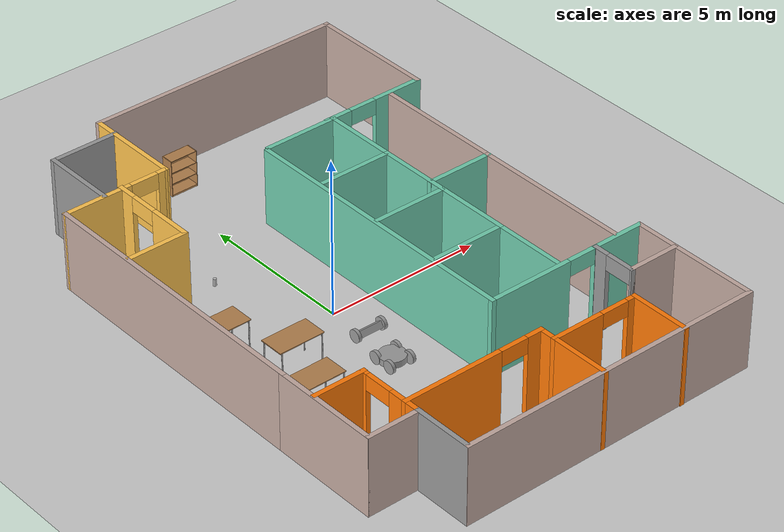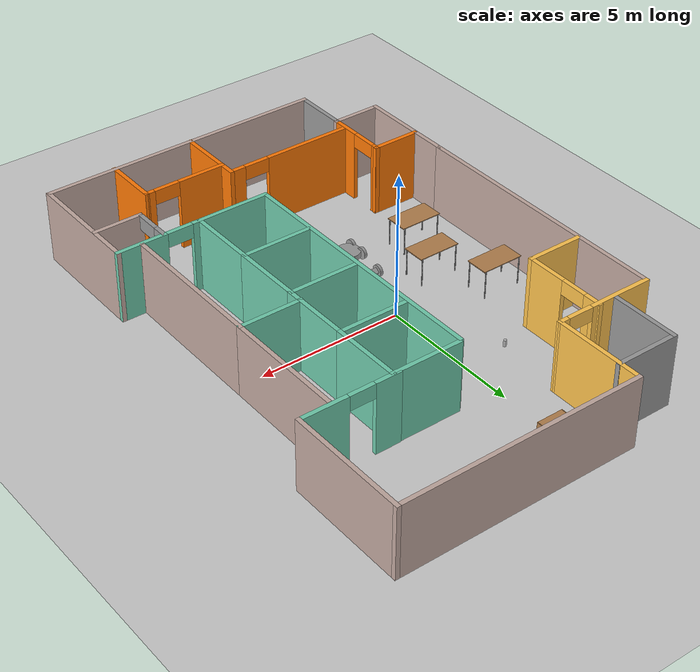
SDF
<sdf version="1.7">
 <world name="default">
  <plugin name="welcome" filename="../build/libwelcome.so"/>
  <light name="sun" type="directional">
   <pose>0 0 10 0 -0 0</pose>
   <diffuse>0.8 0.8 0.8 1</diffuse>
   <specular>0.2 0.2 0.2 1</specular>
   <attenuation>
    <range>1000</range>
    <constant>0.9</constant>
    <linear>0.01</linear>
    <quadratic>0.001</quadratic>
   </attenuation>
   <direction>-0.5 0.1 -0.9</direction>
   <spot><inner_angle>0</inner_angle><outer_angle>0</outer_angle><falloff>0</falloff></spot>
  </light>
  <model name="ground_plane">
   <static>1</static>
   <link name="link">
    <collision name="collision_collision">
     <geometry><plane><normal>0 0 1</normal><size>100 100</size></plane></geometry>
     <surface>
      <contact><collide_bitmask>65535</collide_bitmask></contact>
      <friction><ode><mu>100</mu><mu2>50</mu2></ode></friction>
     </surface>
    </collision>
    <visual name="visual_visual">
     <cast_shadows>0</cast_shadows>
     <geometry><plane><normal>0 0 1</normal><size>100 100</size></plane></geometry>
     <material>
      <script><uri>file://media/materials/scripts/gazebo.material</uri><name>Gazebo/Grey</name></script>
     </material>
    </visual>
   </link>
  </model>
  <gravity>0 0 -9.8</gravity>
  <magnetic_field>6e-06 2.3e-05 -4.2e-05</magnetic_field>
  <atmosphere type="adiabatic"/>
  <physics type="ode">
   <max_step_size>0.001</max_step_size>
   <real_time_factor>1</real_time_factor>
   <real_time_update_rate>1000</real_time_update_rate>
  </physics>
  <scene><ambient>0.4 0.4 0.4 1</ambient><background>0.7 0.7 0.7 1</background><shadows>1</shadows></scene>
  <audio><device>default</device></audio>
  <spherical_coordinates>
   <surface_model>EARTH_WGS84</surface_model>
   <latitude_deg>0</latitude_deg>
   <longitude_deg>0</longitude_deg>
   <elevation>0</elevation>
   <heading_deg>0</heading_deg>
  </spherical_coordinates>
  <model name="mybuilding">
   <pose>1.1462 -0.1123 0 0 -0 0</pose>
   <link name="Wall_123">
    <collision name="collision_Wall_123_Collision">
     <geometry><box><size>5.25 0.15 2.5</size></box></geometry>
     <pose>0 0 1.25 0 -0 0</pose>
    </collision>
    <visual name="visual_Wall_123_Visual">
     <pose>0 0 1.25 0 -0 0</pose>
     <geometry><box><size>5.25 0.15 2.5</size></box></geometry>
     <material>
      <script><uri>file://media/materials/scripts/gazebo.material</uri><name>Gazebo/Grey</name></script>
      <ambient>0.760784 0.662745 0.627451 1</ambient>
     </material>
     <meta><layer>0</layer></meta>
    </visual>
    <pose>4.79444 -2.06703 0 0 -0 1.5708</pose>
   </link>
   <link name="Wall_125">
    <collision name="collision_Wall_125_Collision">
     <geometry><box><size>2.25 0.15 2.5</size></box></geometry>
     <pose>0 0 1.25 0 -0 0</pose>
    </collision>
    <visual name="visual_Wall_125_Visual">
     <pose>0 0 1.25 0 -0 0</pose>
     <geometry><box><size>2.25 0.15 2.5</size></box></geometry>
     <material>
      <script><uri>file://media/materials/scripts/gazebo.material</uri><name>Gazebo/Grey</name></script>
      <ambient>0.435294 0.796078 0.67451 1</ambient>
     </material>
     <meta><layer>0</layer></meta>
    </visual>
    <pose>3.74444 0.482967 0 0 -0 3.14159</pose>
   </link>
   <link name="Wall_127">
    <collision name="collision_Wall_127_Collision">
     <geometry><box><size>4.25 0.15 2.5</size></box></geometry>
     <pose>0 0 1.25 0 -0 0</pose>
    </collision>
    <visual name="visual_Wall_127_Visual">
     <pose>0 0 1.25 0 -0 0</pose>
     <geometry><box><size>4.25 0.15 2.5</size></box></geometry>
     <material>
      <script><uri>file://media/materials/scripts/gazebo.material</uri><name>Gazebo/Grey</name></script>
      <ambient>0.760784 0.662745 0.627451 1</ambient>
     </material>
     <meta><layer>0</layer></meta>
    </visual>
    <pose>4.79444 2.53297 0 0 -0 1.5708</pose>
   </link>
   <link name="Wall_129">
    <collision name="collision_Wall_129_Collision">
     <geometry><box><size>4.25 0.15 2.5</size></box></geometry>
     <pose>0 0 1.25 0 -0 0</pose>
    </collision>
    <visual name="visual_Wall_129_Visual">
     <pose>0 0 1.25 0 -0 0</pose>
     <geometry><box><size>4.25 0.15 2.5</size></box></geometry>
     <material>
      <script><uri>file://media/materials/scripts/gazebo.material</uri><name>Gazebo/Grey</name></script>
      <ambient>0.760784 0.662745 0.627451 1</ambient>
     </material>
     <meta><layer>0</layer></meta>
    </visual>
    <pose>5.86525 6.78658 0 0 -0 1.5708</pose>
   </link>
   <link name="Wall_130">
    <collision name="collision_Wall_130_Collision">
     <geometry><box><size>8.5 0.15 2.5</size></box></geometry>
     <pose>0 0 1.25 0 -0 0</pose>
    </collision>
    <visual name="visual_Wall_130_Visual">
     <pose>0 0 1.25 0 -0 0</pose>
     <geometry><box><size>8.5 0.15 2.5</size></box></geometry>
     <material>
      <script><uri>file://media/materials/scripts/gazebo.material</uri><name>Gazebo/Grey</name></script>
      <ambient>0.760784 0.662745 0.627451 1</ambient>
     </material>
     <meta><layer>0</layer></meta>
    </visual>
    <pose>1.69025 8.83658 0 0 -0 3.14159</pose>
   </link>
   <link name="Wall_131">
    <collision name="collision_Wall_131_Collision">
     <geometry><box><size>3.25 0.15 2.5</size></box></geometry>
     <pose>0 0 1.25 0 -0 0</pose>
    </collision>
    <visual name="visual_Wall_131_Visual">
     <pose>0 0 1.25 0 -0 0</pose>
     <geometry><box><size>3.25 0.15 2.5</size></box></geometry>
     <material>
      <script><uri>file://media/materials/scripts/gazebo.material</uri><name>Gazebo/Grey</name></script>
      <ambient>1 0.764706 0.305882 1</ambient>
     </material>
     <meta><layer>0</layer></meta>
    </visual>
    <pose>-2.48475 7.28658 0 0 -0 -1.5708</pose>
   </link>
   <link name="Wall_136">
    <collision name="collision_Wall_136_Collision">
     <geometry><box><size>9.49958 0.15 2.5</size></box></geometry>
     <pose>0 0 1.25 0 -0 0</pose>
    </collision>
    <visual name="visual_Wall_136_Visual">
     <pose>0 0 1.25 0 -0 0</pose>
     <geometry><box><size>9.49958 0.15 2.5</size></box></geometry>
     <material>
      <script><uri>file://media/materials/scripts/gazebo.material</uri><name>Gazebo/Grey</name></script>
      <ambient>0.760784 0.662745 0.627451 1</ambient>
     </material>
     <meta><layer>0</layer></meta>
    </visual>
    <pose>-5.86518 1.06458 0 0 -0 1.5708</pose>
   </link>
   <link name="Wall_138">
    <pose>-4.17497 5.73808 0 0 -0 3.14071</pose>
    <visual name="visual_Wall_138_Visual_0">
     <pose>-1.57735 0 1.25 0 -0 0</pose>
     <geometry><box><size>0.375734 0.15 2.5</size></box></geometry>
     <material>
      <script><uri>file://media/materials/scripts/gazebo.material</uri><name>Gazebo/Grey</name></script>
      <ambient>1 0.764706 0.305882 1</ambient>
     </material>
     <meta><layer>0</layer></meta>
    </visual>
    <collision name="collision_Wall_138_Collision_0">
     <geometry><box><size>0.375734 0.15 2.5</size></box></geometry>
     <pose>-1.57735 0 1.25 0 -0 0</pose>
    </collision>
    <visual name="visual_Wall_138_Visual_1">
     <pose>0.637867 0 1.25 0 -0 0</pose>
     <geometry><box><size>2.2547 0.15 2.5</size></box></geometry>
     <material>
      <script><uri>file://media/materials/scripts/gazebo.material</uri><name>Gazebo/Grey</name></script>
      <ambient>1 0.764706 0.305882 1</ambient>
     </material>
     <meta><layer>0</layer></meta>
    </visual>
    <collision name="collision_Wall_138_Collision_1">
     <geometry><box><size>2.2547 0.15 2.5</size></box></geometry>
     <pose>0.637867 0 1.25 0 -0 0</pose>
    </collision>
    <visual name="visual_Wall_138_Visual_2">
     <pose>-0.939484 0 2.25 0 -0 0</pose>
     <geometry><box><size>0.9 0.15 0.5</size></box></geometry>
     <material>
      <script><uri>file://media/materials/scripts/gazebo.material</uri><name>Gazebo/Grey</name></script>
      <ambient>1 0.764706 0.305882 1</ambient>
     </material>
     <meta><layer>0</layer></meta>
    </visual>
    <collision name="collision_Wall_138_Collision_2">
     <geometry><box><size>0.9 0.15 0.5</size></box></geometry>
     <pose>-0.939484 0 2.25 0 -0 0</pose>
    </collision>
   </link>
   <link name="Wall_141">
    <collision name="collision_Wall_141_Collision">
     <geometry><box><size>2.25 0.15 2.5</size></box></geometry>
     <pose>0 0 1.25 0 -0 0</pose>
    </collision>
    <visual name="visual_Wall_141_Visual">
     <pose>0 0 1.25 0 -0 0</pose>
     <geometry><box><size>2.25 0.15 2.5</size></box></geometry>
     <material>
      <script><uri>file://media/materials/scripts/gazebo.material</uri><name>Gazebo/Grey</name></script>
      <ambient>1 1 1 1</ambient>
     </material>
     <meta><layer>0</layer></meta>
    </visual>
    <pose>-3.51661 8.10127 0 0 -0 3.14159</pose>
   </link>
   <link name="Wall_142">
    <collision name="collision_Wall_142_Collision">
     <geometry><box><size>2.5 0.15 2.5</size></box></geometry>
     <pose>0 0 1.25 0 -0 0</pose>
    </collision>
    <visual name="visual_Wall_142_Visual">
     <pose>0 0 1.25 0 -0 0</pose>
     <geometry><box><size>2.5 0.15 2.5</size></box></geometry>
     <material>
      <script><uri>file://media/materials/scripts/gazebo.material</uri><name>Gazebo/Grey</name></script>
      <ambient>1 1 1 1</ambient>
     </material>
     <meta><layer>0</layer></meta>
    </visual>
    <pose>-4.56661 6.92627 0 0 -0 -1.5708</pose>
   </link>
   <link name="Wall_144">
    <pose>-3.95132 4.36352 0 0 -0 -1.5708</pose>
    <visual name="visual_Wall_144_Visual_0">
     <pose>-1.17446 0 1.25 0 -0 0</pose>
     <geometry><box><size>0.651089 0.15 2.5</size></box></geometry>
     <material>
      <script><uri>file://media/materials/scripts/gazebo.material</uri><name>Gazebo/Grey</name></script>
      <ambient>1 0.764706 0.305882 1</ambient>
     </material>
     <meta><layer>0</layer></meta>
    </visual>
    <collision name="collision_Wall_144_Collision_0">
     <geometry><box><size>0.651089 0.15 2.5</size></box></geometry>
     <pose>-1.17446 0 1.25 0 -0 0</pose>
    </collision>
    <visual name="visual_Wall_144_Visual_1">
     <pose>0.775545 0 1.25 0 -0 0</pose>
     <geometry><box><size>1.44891 0.15 2.5</size></box></geometry>
     <material>
      <script><uri>file://media/materials/scripts/gazebo.material</uri><name>Gazebo/Grey</name></script>
      <ambient>1 0.764706 0.305882 1</ambient>
     </material>
     <meta><layer>0</layer></meta>
    </visual>
    <collision name="collision_Wall_144_Collision_1">
     <geometry><box><size>1.44891 0.15 2.5</size></box></geometry>
     <pose>0.775545 0 1.25 0 -0 0</pose>
    </collision>
    <visual name="visual_Wall_144_Visual_2">
     <pose>-0.398911 0 2.25 0 -0 0</pose>
     <geometry><box><size>0.9 0.15 0.5</size></box></geometry>
     <material>
      <script><uri>file://media/materials/scripts/gazebo.material</uri><name>Gazebo/Grey</name></script>
      <ambient>1 0.764706 0.305882 1</ambient>
     </material>
     <meta><layer>0</layer></meta>
    </visual>
    <collision name="collision_Wall_144_Collision_2">
     <geometry><box><size>0.9 0.15 0.5</size></box></geometry>
     <pose>-0.398911 0 2.25 0 -0 0</pose>
    </collision>
   </link>
   <link name="Wall_145">
    <collision name="collision_Wall_145_Collision">
     <geometry><box><size>2 0.15 2.5</size></box></geometry>
     <pose>0 0 1.25 0 -0 0</pose>
    </collision>
    <visual name="visual_Wall_145_Visual">
     <pose>0 0 1.25 0 -0 0</pose>
     <geometry><box><size>2 0.15 2.5</size></box></geometry>
     <material>
      <script><uri>file://media/materials/scripts/gazebo.material</uri><name>Gazebo/Grey</name></script>
      <ambient>1 0.764706 0.305882 1</ambient>
     </material>
     <meta><layer>0</layer></meta>
    </visual>
    <pose>-4.87632 2.93852 0 0 -0 3.14159</pose>
   </link>
   <link name="Wall_27">
    <collision name="collision_Wall_27_Collision">
     <geometry><box><size>1.9915 0.15 2.5</size></box></geometry>
     <pose>0 0 1.25 0 -0 0</pose>
    </collision>
    <visual name="visual_Wall_27_Visual">
     <pose>0 0 1.25 0 -0 0</pose>
     <geometry><box><size>1.9915 0.15 2.5</size></box></geometry>
     <material>
      <script><uri>file://media/materials/scripts/gazebo.material</uri><name>Gazebo/Grey</name></script>
      <ambient>1 1 1 1</ambient>
     </material>
     <meta><layer>0</layer></meta>
    </visual>
    <pose>-4.23475 -7.88117 0 0 -0 -1.5708</pose>
   </link>
   <link name="Wall_36">
    <pose>-4.23475 -5.89742 0 0 -0 1.5708</pose>
    <visual name="visual_Wall_36_Visual_0">
     <pose>-0.580632 0 1.25 0 -0 0</pose>
     <geometry><box><size>1.11474 0.15 2.5</size></box></geometry>
     <material>
      <script><uri>file://media/materials/scripts/gazebo.material</uri><name>Gazebo/Grey</name></script>
      <ambient>0.996078 0.47451 0.0196078 1</ambient>
     </material>
     <meta><layer>0</layer></meta>
    </visual>
    <collision name="collision_Wall_36_Collision_0">
     <geometry><box><size>1.11474 0.15 2.5</size></box></geometry>
     <pose>-0.580632 0 1.25 0 -0 0</pose>
    </collision>
    <visual name="visual_Wall_36_Visual_1">
     <pose>1.00737 0 1.25 0 -0 0</pose>
     <geometry><box><size>0.261265 0.15 2.5</size></box></geometry>
     <material>
      <script><uri>file://media/materials/scripts/gazebo.material</uri><name>Gazebo/Grey</name></script>
      <ambient>0.996078 0.47451 0.0196078 1</ambient>
     </material>
     <meta><layer>0</layer></meta>
    </visual>
    <collision name="collision_Wall_36_Collision_1">
     <geometry><box><size>0.261265 0.15 2.5</size></box></geometry>
     <pose>1.00737 0 1.25 0 -0 0</pose>
    </collision>
    <visual name="visual_Wall_36_Visual_2">
     <pose>0.426735 0 2.25 0 -0 0</pose>
     <geometry><box><size>0.9 0.15 0.5</size></box></geometry>
     <material>
      <script><uri>file://media/materials/scripts/gazebo.material</uri><name>Gazebo/Grey</name></script>
      <ambient>0.996078 0.47451 0.0196078 1</ambient>
     </material>
     <meta><layer>0</layer></meta>
    </visual>
    <collision name="collision_Wall_36_Collision_2">
     <geometry><box><size>0.9 0.15 0.5</size></box></geometry>
     <pose>0.426735 0 2.25 0 -0 0</pose>
    </collision>
   </link>
   <link name="Wall_41">
    <collision name="collision_Wall_41_Collision">
     <geometry><box><size>1.75 0.15 2.5</size></box></geometry>
     <pose>0 0 1.25 0 -0 0</pose>
    </collision>
    <visual name="visual_Wall_41_Visual">
     <pose>0 0 1.25 0 -0 0</pose>
     <geometry><box><size>1.75 0.15 2.5</size></box></geometry>
     <material>
      <script><uri>file://media/materials/scripts/gazebo.material</uri><name>Gazebo/Grey</name></script>
      <ambient>0.996078 0.47451 0.0196078 1</ambient>
     </material>
     <meta><layer>0</layer></meta>
    </visual>
    <pose>-5.02325 -4.83442 0 0 -0 3.14159</pose>
   </link>
   <link name="Wall_43">
    <collision name="collision_Wall_43_Collision">
     <geometry><box><size>10 0.15 2.5</size></box></geometry>
     <pose>0 0 1.25 0 -0 0</pose>
    </collision>
    <visual name="visual_Wall_43_Visual">
     <pose>0 0 1.25 0 -0 0</pose>
     <geometry><box><size>10 0.15 2.5</size></box></geometry>
     <material>
      <script><uri>file://media/materials/scripts/gazebo.material</uri><name>Gazebo/Grey</name></script>
      <ambient>0.760784 0.662745 0.627451 1</ambient>
     </material>
     <meta><layer>0</layer></meta>
    </visual>
    <pose>0.690251 -8.81342 0 0 -0 0</pose>
   </link>
   <link name="Wall_47">
    <pose>-1.93659 -6.46908 0 0 -0 0</pose>
    <visual name="visual_Wall_47_Visual_0">
     <pose>-0.7455 0 1.25 0 -0 0</pose>
     <geometry><box><size>3.259 0.15 2.5</size></box></geometry>
     <material>
      <script><uri>file://media/materials/scripts/gazebo.material</uri><name>Gazebo/Grey</name></script>
      <ambient>0.996078 0.47451 0.0196078 1</ambient>
     </material>
     <meta><layer>0</layer></meta>
    </visual>
    <collision name="collision_Wall_47_Collision_0">
     <geometry><box><size>3.259 0.15 2.5</size></box></geometry>
     <pose>-0.7455 0 1.25 0 -0 0</pose>
    </collision>
    <visual name="visual_Wall_47_Visual_1">
     <pose>2.0795 0 1.25 0 -0 0</pose>
     <geometry><box><size>0.591 0.15 2.5</size></box></geometry>
     <material>
      <script><uri>file://media/materials/scripts/gazebo.material</uri><name>Gazebo/Grey</name></script>
      <ambient>0.996078 0.47451 0.0196078 1</ambient>
     </material>
     <meta><layer>0</layer></meta>
    </visual>
    <collision name="collision_Wall_47_Collision_1">
     <geometry><box><size>0.591 0.15 2.5</size></box></geometry>
     <pose>2.0795 0 1.25 0 -0 0</pose>
    </collision>
    <visual name="visual_Wall_47_Visual_2">
     <pose>1.334 0 2.25 0 -0 0</pose>
     <geometry><box><size>0.9 0.15 0.5</size></box></geometry>
     <material>
      <script><uri>file://media/materials/scripts/gazebo.material</uri><name>Gazebo/Grey</name></script>
      <ambient>0.996078 0.47451 0.0196078 1</ambient>
     </material>
     <meta><layer>0</layer></meta>
    </visual>
    <collision name="collision_Wall_47_Collision_2">
     <geometry><box><size>0.9 0.15 0.5</size></box></geometry>
     <pose>1.334 0 2.25 0 -0 0</pose>
    </collision>
   </link>
   <link name="Wall_48">
    <collision name="collision_Wall_48_Collision">
     <geometry><box><size>2.5 0.15 2.5</size></box></geometry>
     <pose>0 0 1.25 0 -0 0</pose>
    </collision>
    <visual name="visual_Wall_48_Visual">
     <pose>0 0 1.25 0 -0 0</pose>
     <geometry><box><size>2.5 0.15 2.5</size></box></geometry>
     <material>
      <script><uri>file://media/materials/scripts/gazebo.material</uri><name>Gazebo/Grey</name></script>
      <ambient>0.996078 0.47451 0.0196078 1</ambient>
     </material>
     <meta><layer>0</layer></meta>
    </visual>
    <pose>0.36341 -7.64408 0 0 -0 -1.5708</pose>
   </link>
   <link name="Wall_52">
    <pose>1.78841 -6.98658 0 0 -0 0</pose>
    <visual name="visual_Wall_52_Visual_0">
     <pose>-0.63525 0 1.25 0 -0 0</pose>
     <geometry><box><size>1.7295 0.15 2.5</size></box></geometry>
     <material>
      <script><uri>file://media/materials/scripts/gazebo.material</uri><name>Gazebo/Grey</name></script>
      <ambient>0.996078 0.47451 0.0196078 1</ambient>
     </material>
     <meta><layer>0</layer></meta>
    </visual>
    <collision name="collision_Wall_52_Collision_0">
     <geometry><box><size>1.7295 0.15 2.5</size></box></geometry>
     <pose>-0.63525 0 1.25 0 -0 0</pose>
    </collision>
    <visual name="visual_Wall_52_Visual_1">
     <pose>1.31475 0 1.25 0 -0 0</pose>
     <geometry><box><size>0.3705 0.15 2.5</size></box></geometry>
     <material>
      <script><uri>file://media/materials/scripts/gazebo.material</uri><name>Gazebo/Grey</name></script>
      <ambient>0.996078 0.47451 0.0196078 1</ambient>
     </material>
     <meta><layer>0</layer></meta>
    </visual>
    <collision name="collision_Wall_52_Collision_1">
     <geometry><box><size>0.3705 0.15 2.5</size></box></geometry>
     <pose>1.31475 0 1.25 0 -0 0</pose>
    </collision>
    <visual name="visual_Wall_52_Visual_2">
     <pose>0.6795 0 2.25 0 -0 0</pose>
     <geometry><box><size>0.9 0.15 0.5</size></box></geometry>
     <material>
      <script><uri>file://media/materials/scripts/gazebo.material</uri><name>Gazebo/Grey</name></script>
      <ambient>0.996078 0.47451 0.0196078 1</ambient>
     </material>
     <meta><layer>0</layer></meta>
    </visual>
    <collision name="collision_Wall_52_Collision_2">
     <geometry><box><size>0.9 0.15 0.5</size></box></geometry>
     <pose>0.6795 0 2.25 0 -0 0</pose>
    </collision>
   </link>
   <link name="Wall_53">
    <collision name="collision_Wall_53_Collision">
     <geometry><box><size>2 0.15 2.5</size></box></geometry>
     <pose>0 0 1.25 0 -0 0</pose>
    </collision>
    <visual name="visual_Wall_53_Visual">
     <pose>0 0 1.25 0 -0 0</pose>
     <geometry><box><size>2 0.15 2.5</size></box></geometry>
     <material>
      <script><uri>file://media/materials/scripts/gazebo.material</uri><name>Gazebo/Grey</name></script>
      <ambient>0.996078 0.47451 0.0196078 1</ambient>
     </material>
     <meta><layer>0</layer></meta>
    </visual>
    <pose>3.21341 -7.91158 0 0 -0 -1.5708</pose>
   </link>
   <link name="Wall_55">
    <collision name="collision_Wall_55_Collision">
     <geometry><box><size>4.25 0.15 2.5</size></box></geometry>
     <pose>0 0 1.25 0 -0 0</pose>
    </collision>
    <visual name="visual_Wall_55_Visual">
     <pose>0 0 1.25 0 -0 0</pose>
     <geometry><box><size>4.25 0.15 2.5</size></box></geometry>
     <material>
      <script><uri>file://media/materials/scripts/gazebo.material</uri><name>Gazebo/Grey</name></script>
      <ambient>0.760784 0.662745 0.627451 1</ambient>
     </material>
     <meta><layer>0</layer></meta>
    </visual>
    <pose>5.61525 -6.76342 0 0 -0 1.5708</pose>
   </link>
   <link name="Wall_56">
    <pose>2.94025 -4.71342 0 0 -0 3.14159</pose>
    <visual name="visual_Wall_56_Visual_0">
     <pose>-1.85364 0 1.25 0 -0 0</pose>
     <geometry><box><size>1.79272 0.15 2.5</size></box></geometry>
     <material>
      <script><uri>file://media/materials/scripts/gazebo.material</uri><name>Gazebo/Grey</name></script>
      <ambient>0.435294 0.796078 0.67451 1</ambient>
     </material>
     <meta><layer>0</layer></meta>
    </visual>
    <collision name="collision_Wall_56_Collision_0">
     <geometry><box><size>1.79272 0.15 2.5</size></box></geometry>
     <pose>-1.85364 0 1.25 0 -0 0</pose>
    </collision>
    <visual name="visual_Wall_56_Visual_1">
     <pose>1.34636 0 1.25 0 -0 0</pose>
     <geometry><box><size>2.80728 0.15 2.5</size></box></geometry>
     <material>
      <script><uri>file://media/materials/scripts/gazebo.material</uri><name>Gazebo/Grey</name></script>
      <ambient>0.435294 0.796078 0.67451 1</ambient>
     </material>
     <meta><layer>0</layer></meta>
    </visual>
    <collision name="collision_Wall_56_Collision_1">
     <geometry><box><size>2.80728 0.15 2.5</size></box></geometry>
     <pose>1.34636 0 1.25 0 -0 0</pose>
    </collision>
    <visual name="visual_Wall_56_Visual_2">
     <pose>-0.507283 0 2.25 0 -0 0</pose>
     <geometry><box><size>0.9 0.15 0.5</size></box></geometry>
     <material>
      <script><uri>file://media/materials/scripts/gazebo.material</uri><name>Gazebo/Grey</name></script>
      <ambient>0.435294 0.796078 0.67451 1</ambient>
     </material>
     <meta><layer>0</layer></meta>
    </visual>
    <collision name="collision_Wall_56_Collision_2">
     <geometry><box><size>0.9 0.15 0.5</size></box></geometry>
     <pose>-0.507283 0 2.25 0 -0 0</pose>
    </collision>
   </link>
   <link name="Wall_58">
    <collision name="collision_Wall_58_Collision">
     <geometry><box><size>1.75 0.15 2.5</size></box></geometry>
     <pose>0 0 1.25 0 -0 0</pose>
    </collision>
    <visual name="visual_Wall_58_Visual">
     <pose>0 0 1.25 0 -0 0</pose>
     <geometry><box><size>1.75 0.15 2.5</size></box></geometry>
     <material>
      <script><uri>file://media/materials/scripts/gazebo.material</uri><name>Gazebo/Grey</name></script>
      <ambient>0.760784 0.662745 0.627451 1</ambient>
     </material>
     <meta><layer>0</layer></meta>
    </visual>
    <pose>4.79591 -6.07808 0 0 -0 3.14159</pose>
   </link>
   <link name="Wall_59">
    <pose>3.98441 -5.40308 0 0 -0 1.5708</pose>
    <visual name="visual_Wall_59_Visual_0">
     <pose>-0.719 0 1.25 0 -0 0</pose>
     <geometry><box><size>0.062 0.15 2.5</size></box></geometry>
     <material>
      <script><uri>file://media/materials/scripts/gazebo.material</uri><name>Gazebo/Grey</name></script>
      <ambient>1 1 1 1</ambient>
     </material>
     <meta><layer>0</layer></meta>
    </visual>
    <collision name="collision_Wall_59_Collision_0">
     <geometry><box><size>0.062 0.15 2.5</size></box></geometry>
     <pose>-0.719 0 1.25 0 -0 0</pose>
    </collision>
    <visual name="visual_Wall_59_Visual_1">
     <pose>0.481 0 1.25 0 -0 0</pose>
     <geometry><box><size>0.538 0.15 2.5</size></box></geometry>
     <material>
      <script><uri>file://media/materials/scripts/gazebo.material</uri><name>Gazebo/Grey</name></script>
      <ambient>1 1 1 1</ambient>
     </material>
     <meta><layer>0</layer></meta>
    </visual>
    <collision name="collision_Wall_59_Collision_1">
     <geometry><box><size>0.538 0.15 2.5</size></box></geometry>
     <pose>0.481 0 1.25 0 -0 0</pose>
    </collision>
    <visual name="visual_Wall_59_Visual_2">
     <pose>-0.238 0 2.25 0 -0 0</pose>
     <geometry><box><size>0.9 0.15 0.5</size></box></geometry>
     <material>
      <script><uri>file://media/materials/scripts/gazebo.material</uri><name>Gazebo/Grey</name></script>
      <ambient>1 1 1 1</ambient>
     </material>
     <meta><layer>0</layer></meta>
    </visual>
    <collision name="collision_Wall_59_Collision_2">
     <geometry><box><size>0.9 0.15 0.5</size></box></geometry>
     <pose>-0.238 0 2.25 0 -0 0</pose>
    </collision>
   </link>
   <link name="Wall_6">
    <collision name="collision_Wall_6_Collision">
     <geometry><box><size>3.5 0.15 2.5</size></box></geometry>
     <pose>0 0 1.25 0 -0 0</pose>
    </collision>
    <visual name="visual_Wall_6_Visual">
     <pose>0 0 1.25 0 -0 0</pose>
     <geometry><box><size>3.5 0.15 2.5</size></box></geometry>
     <material>
      <script><uri>file://media/materials/scripts/gazebo.material</uri><name>Gazebo/Grey</name></script>
      <ambient>0.760784 0.662745 0.627451 1</ambient>
     </material>
     <meta><layer>0</layer></meta>
    </visual>
    <pose>-5.86518 -5.28542 0 0 -0 -1.5708</pose>
   </link>
   <link name="Wall_73">
    <collision name="collision_Wall_73_Collision">
     <geometry><box><size>2.5 0.15 2.5</size></box></geometry>
     <pose>0 0 1.25 0 -0 0</pose>
    </collision>
    <visual name="visual_Wall_73_Visual">
     <pose>0 0 1.25 0 -0 0</pose>
     <geometry><box><size>2.5 0.15 2.5</size></box></geometry>
     <material>
      <script><uri>file://media/materials/scripts/gazebo.material</uri><name>Gazebo/Grey</name></script>
      <ambient>0.435294 0.796078 0.67451 1</ambient>
     </material>
     <meta><layer>0</layer></meta>
    </visual>
    <pose>2.70558 -3.51332 0 0 -0 1.5708</pose>
   </link>
   <link name="Wall_74">
    <collision name="collision_Wall_74_Collision">
     <geometry><box><size>2.5 0.15 2.5</size></box></geometry>
     <pose>0 0 1.25 0 -0 0</pose>
    </collision>
    <visual name="visual_Wall_74_Visual">
     <pose>0 0 1.25 0 -0 0</pose>
     <geometry><box><size>2.5 0.15 2.5</size></box></geometry>
     <material>
      <script><uri>file://media/materials/scripts/gazebo.material</uri><name>Gazebo/Grey</name></script>
      <ambient>0.435294 0.796078 0.67451 1</ambient>
     </material>
     <meta><layer>0</layer></meta>
    </visual>
    <pose>1.53058 -2.33832 0 0 -0 3.14159</pose>
   </link>
   <link name="Wall_76">
    <collision name="collision_Wall_76_Collision">
     <geometry><box><size>2.5 0.15 2.5</size></box></geometry>
     <pose>0 0 1.25 0 -0 0</pose>
    </collision>
    <visual name="visual_Wall_76_Visual">
     <pose>0 0 1.25 0 -0 0</pose>
     <geometry><box><size>2.5 0.15 2.5</size></box></geometry>
     <material>
      <script><uri>file://media/materials/scripts/gazebo.material</uri><name>Gazebo/Grey</name></script>
      <ambient>0.435294 0.796078 0.67451 1</ambient>
     </material>
     <meta><layer>0</layer></meta>
    </visual>
    <pose>2.70558 -1.16332 0 0 -0 1.5708</pose>
   </link>
   <link name="Wall_77">
    <collision name="collision_Wall_77_Collision">
     <geometry><box><size>2.5 0.15 2.5</size></box></geometry>
     <pose>0 0 1.25 0 -0 0</pose>
    </collision>
    <visual name="visual_Wall_77_Visual">
     <pose>0 0 1.25 0 -0 0</pose>
     <geometry><box><size>2.5 0.15 2.5</size></box></geometry>
     <material>
      <script><uri>file://media/materials/scripts/gazebo.material</uri><name>Gazebo/Grey</name></script>
      <ambient>0.435294 0.796078 0.67451 1</ambient>
     </material>
     <meta><layer>0</layer></meta>
    </visual>
    <pose>1.53058 0.011678 0 0 -0 3.14159</pose>
   </link>
   <link name="Wall_79">
    <collision name="collision_Wall_79_Collision">
     <geometry><box><size>2.5 0.15 2.5</size></box></geometry>
     <pose>0 0 1.25 0 -0 0</pose>
    </collision>
    <visual name="visual_Wall_79_Visual">
     <pose>0 0 1.25 0 -0 0</pose>
     <geometry><box><size>2.5 0.15 2.5</size></box></geometry>
     <material>
      <script><uri>file://media/materials/scripts/gazebo.material</uri><name>Gazebo/Grey</name></script>
      <ambient>0.435294 0.796078 0.67451 1</ambient>
     </material>
     <meta><layer>0</layer></meta>
    </visual>
    <pose>2.70558 1.18668 0 0 -0 1.5708</pose>
   </link>
   <link name="Wall_8">
    <collision name="collision_Wall_8_Collision">
     <geometry><box><size>1.78043 0.15 2.5</size></box></geometry>
     <pose>0 0 1.25 0 -0 0</pose>
    </collision>
    <visual name="visual_Wall_8_Visual">
     <pose>0 0 1.25 0 -0 0</pose>
     <geometry><box><size>1.78043 0.15 2.5</size></box></geometry>
     <material>
      <script><uri>file://media/materials/scripts/gazebo.material</uri><name>Gazebo/Grey</name></script>
      <ambient>0.760784 0.662745 0.627451 1</ambient>
     </material>
     <meta><layer>0</layer></meta>
    </visual>
    <pose>-5.04127 -6.96042 0 0 -0 0</pose>
   </link>
   <link name="Wall_82">
    <collision name="collision_Wall_82_Collision">
     <geometry><box><size>2.5 0.15 2.5</size></box></geometry>
     <pose>0 0 1.25 0 -0 0</pose>
    </collision>
    <visual name="visual_Wall_82_Visual">
     <pose>0 0 1.25 0 -0 0</pose>
     <geometry><box><size>2.5 0.15 2.5</size></box></geometry>
     <material>
      <script><uri>file://media/materials/scripts/gazebo.material</uri><name>Gazebo/Grey</name></script>
      <ambient>0.435294 0.796078 0.67451 1</ambient>
     </material>
     <meta><layer>0</layer></meta>
    </visual>
    <pose>1.53058 2.36168 0 0 -0 3.14159</pose>
   </link>
   <link name="Wall_85">
    <collision name="collision_Wall_85_Collision">
     <geometry><box><size>2.5 0.15 2.5</size></box></geometry>
     <pose>0 0 1.25 0 -0 0</pose>
    </collision>
    <visual name="visual_Wall_85_Visual">
     <pose>0 0 1.25 0 -0 0</pose>
     <geometry><box><size>2.5 0.15 2.5</size></box></geometry>
     <material>
      <script><uri>file://media/materials/scripts/gazebo.material</uri><name>Gazebo/Grey</name></script>
      <ambient>0.435294 0.796078 0.67451 1</ambient>
     </material>
     <meta><layer>0</layer></meta>
    </visual>
    <pose>2.70558 3.53668 0 0 -0 1.5708</pose>
   </link>
   <link name="Wall_86">
    <collision name="collision_Wall_86_Collision">
     <geometry><box><size>2.5 0.15 2.5</size></box></geometry>
     <pose>0 0 1.25 0 -0 0</pose>
    </collision>
    <visual name="visual_Wall_86_Visual">
     <pose>0 0 1.25 0 -0 0</pose>
     <geometry><box><size>2.5 0.15 2.5</size></box></geometry>
     <material>
      <script><uri>file://media/materials/scripts/gazebo.material</uri><name>Gazebo/Grey</name></script>
      <ambient>0.435294 0.796078 0.67451 1</ambient>
     </material>
     <meta><layer>0</layer></meta>
    </visual>
    <pose>1.53058 4.71168 0 0 -0 3.14159</pose>
   </link>
   <link name="Wall_88">
    <collision name="collision_Wall_88_Collision">
     <geometry><box><size>9.5 0.15 2.5</size></box></geometry>
     <pose>0 0 1.25 0 -0 0</pose>
    </collision>
    <visual name="visual_Wall_88_Visual">
     <pose>0 0 1.25 0 -0 0</pose>
     <geometry><box><size>9.5 0.15 2.5</size></box></geometry>
     <material>
      <script><uri>file://media/materials/scripts/gazebo.material</uri><name>Gazebo/Grey</name></script>
      <ambient>0.435294 0.796078 0.67451 1</ambient>
     </material>
     <meta><layer>0</layer></meta>
    </visual>
    <pose>0.265251 -0.038418 0 0 -0 1.5708</pose>
   </link>
   <link name="Wall_93">
    <pose>4.19025 4.73658 0 0 -0 3.14159</pose>
    <visual name="visual_Wall_93_Visual_0">
     <pose>-0.901489 0 1.25 0 -0 0</pose>
     <geometry><box><size>1.69702 0.15 2.5</size></box></geometry>
     <material>
      <script><uri>file://media/materials/scripts/gazebo.material</uri><name>Gazebo/Grey</name></script>
      <ambient>0.435294 0.796078 0.67451 1</ambient>
     </material>
     <meta><layer>0</layer></meta>
    </visual>
    <collision name="collision_Wall_93_Collision_0">
     <geometry><box><size>1.69702 0.15 2.5</size></box></geometry>
     <pose>-0.901489 0 1.25 0 -0 0</pose>
    </collision>
    <visual name="visual_Wall_93_Visual_1">
     <pose>1.29851 0 1.25 0 -0 0</pose>
     <geometry><box><size>0.902978 0.15 2.5</size></box></geometry>
     <material>
      <script><uri>file://media/materials/scripts/gazebo.material</uri><name>Gazebo/Grey</name></script>
      <ambient>0.435294 0.796078 0.67451 1</ambient>
     </material>
     <meta><layer>0</layer></meta>
    </visual>
    <collision name="collision_Wall_93_Collision_1">
     <geometry><box><size>0.902978 0.15 2.5</size></box></geometry>
     <pose>1.29851 0 1.25 0 -0 0</pose>
    </collision>
    <visual name="visual_Wall_93_Visual_2">
     <pose>0.397022 0 2.25 0 -0 0</pose>
     <geometry><box><size>0.9 0.15 0.5</size></box></geometry>
     <material>
      <script><uri>file://media/materials/scripts/gazebo.material</uri><name>Gazebo/Grey</name></script>
      <ambient>0.435294 0.796078 0.67451 1</ambient>
     </material>
     <meta><layer>0</layer></meta>
    </visual>
    <collision name="collision_Wall_93_Collision_2">
     <geometry><box><size>0.9 0.15 0.5</size></box></geometry>
     <pose>0.397022 0 2.25 0 -0 0</pose>
    </collision>
   </link>
   <static>1</static>
  </model>
  <model name="table">
   <static>1</static>
   <link name="link">
    <collision name="collision_surface">
     <pose>0 0 1 0 -0 0</pose>
     <geometry><box><size>1.5 0.8 0.03</size></box></geometry>
     <surface><friction><ode><mu>0.6</mu><mu2>0.6</mu2></ode></friction></surface>
    </collision>
    <visual name="visual_visual1">
     <pose>0 0 1 0 -0 0</pose>
     <geometry><box><size>1.5 0.8 0.03</size></box></geometry>
     <material>
      <script><uri>file://media/materials/scripts/gazebo.material</uri><name>Gazebo/Wood</name></script>
     </material>
    </visual>
    <collision name="collision_collision_front_left_leg">
     <pose>0.68 0.38 0.5 0 -0 0</pose>
     <geometry><cylinder><radius>0.02</radius><length>1</length></cylinder></geometry>
    </collision>
    <visual name="visual_visual_front_left_leg">
     <pose>0.68 0.38 0.5 0 -0 0</pose>
     <geometry><cylinder><radius>0.02</radius><length>1</length></cylinder></geometry>
     <material>
      <script><uri>file://media/materials/scripts/gazebo.material</uri><name>Gazebo/Grey</name></script>
     </material>
    </visual>
    <collision name="collision_collision_front_right_leg">
     <pose>0.68 -0.38 0.5 0 -0 0</pose>
     <geometry><cylinder><radius>0.02</radius><length>1</length></cylinder></geometry>
    </collision>
    <visual name="visual_visual_front_right_leg">
     <pose>0.68 -0.38 0.5 0 -0 0</pose>
     <geometry><cylinder><radius>0.02</radius><length>1</length></cylinder></geometry>
     <material>
      <script><uri>file://media/materials/scripts/gazebo.material</uri><name>Gazebo/Grey</name></script>
     </material>
    </visual>
    <collision name="collision_back_right_leg">
     <pose>-0.68 -0.38 0.5 0 -0 0</pose>
     <geometry><cylinder><radius>0.02</radius><length>1</length></cylinder></geometry>
    </collision>
    <visual name="visual_back_right_leg">
     <pose>-0.68 -0.38 0.5 0 -0 0</pose>
     <geometry><cylinder><radius>0.02</radius><length>1</length></cylinder></geometry>
     <material>
      <script><uri>file://media/materials/scripts/gazebo.material</uri><name>Gazebo/Grey</name></script>
     </material>
    </visual>
    <collision name="collision_back_left_leg">
     <pose>-0.68 0.38 0.5 0 -0 0</pose>
     <geometry><cylinder><radius>0.02</radius><length>1</length></cylinder></geometry>
    </collision>
    <visual name="visual_back_left_leg">
     <pose>-0.68 0.38 0.5 0 -0 0</pose>
     <geometry><cylinder><radius>0.02</radius><length>1</length></cylinder></geometry>
     <material>
      <script><uri>file://media/materials/scripts/gazebo.material</uri><name>Gazebo/Grey</name></script>
     </material>
    </visual>
   </link>
   <pose>-3.42213 0.583745 0 0 -0 0</pose>
  </model>
  <model name="table_0">
   <static>1</static>
   <link name="link">
    <collision name="collision_surface">
     <pose>0 0 1 0 -0 0</pose>
     <geometry><box><size>1.5 0.8 0.03</size></box></geometry>
     <surface><friction><ode><mu>0.6</mu><mu2>0.6</mu2></ode></friction></surface>
    </collision>
    <visual name="visual_visual1">
     <pose>0 0 1 0 -0 0</pose>
     <geometry><box><size>1.5 0.8 0.03</size></box></geometry>
     <material>
      <script><uri>file://media/materials/scripts/gazebo.material</uri><name>Gazebo/Wood</name></script>
     </material>
    </visual>
    <collision name="collision_collision_front_left_leg">
     <pose>0.68 0.38 0.5 0 -0 0</pose>
     <geometry><cylinder><radius>0.02</radius><length>1</length></cylinder></geometry>
    </collision>
    <visual name="visual_visual_front_left_leg">
     <pose>0.68 0.38 0.5 0 -0 0</pose>
     <geometry><cylinder><radius>0.02</radius><length>1</length></cylinder></geometry>
     <material>
      <script><uri>file://media/materials/scripts/gazebo.material</uri><name>Gazebo/Grey</name></script>
     </material>
    </visual>
    <collision name="collision_collision_front_right_leg">
     <pose>0.68 -0.38 0.5 0 -0 0</pose>
     <geometry><cylinder><radius>0.02</radius><length>1</length></cylinder></geometry>
    </collision>
    <visual name="visual_visual_front_right_leg">
     <pose>0.68 -0.38 0.5 0 -0 0</pose>
     <geometry><cylinder><radius>0.02</radius><length>1</length></cylinder></geometry>
     <material>
      <script><uri>file://media/materials/scripts/gazebo.material</uri><name>Gazebo/Grey</name></script>
     </material>
    </visual>
    <collision name="collision_back_right_leg">
     <pose>-0.68 -0.38 0.5 0 -0 0</pose>
     <geometry><cylinder><radius>0.02</radius><length>1</length></cylinder></geometry>
    </collision>
    <visual name="visual_back_right_leg">
     <pose>-0.68 -0.38 0.5 0 -0 0</pose>
     <geometry><cylinder><radius>0.02</radius><length>1</length></cylinder></geometry>
     <material>
      <script><uri>file://media/materials/scripts/gazebo.material</uri><name>Gazebo/Grey</name></script>
     </material>
    </visual>
    <collision name="collision_back_left_leg">
     <pose>-0.68 0.38 0.5 0 -0 0</pose>
     <geometry><cylinder><radius>0.02</radius><length>1</length></cylinder></geometry>
    </collision>
    <visual name="visual_back_left_leg">
     <pose>-0.68 0.38 0.5 0 -0 0</pose>
     <geometry><cylinder><radius>0.02</radius><length>1</length></cylinder></geometry>
     <material>
      <script><uri>file://media/materials/scripts/gazebo.material</uri><name>Gazebo/Grey</name></script>
     </material>
    </visual>
   </link>
   <pose>-2.29771 -1.11789 0 0 -0 0</pose>
  </model>
  <model name="table_1">
   <static>1</static>
   <link name="link">
    <collision name="collision_surface">
     <pose>0 0 1 0 -0 0</pose>
     <geometry><box><size>1.5 0.8 0.03</size></box></geometry>
     <surface><friction><ode><mu>0.6</mu><mu2>0.6</mu2></ode></friction></surface>
    </collision>
    <visual name="visual_visual1">
     <pose>0 0 1 0 -0 0</pose>
     <geometry><box><size>1.5 0.8 0.03</size></box></geometry>
     <material>
      <script><uri>file://media/materials/scripts/gazebo.material</uri><name>Gazebo/Wood</name></script>
     </material>
    </visual>
    <collision name="collision_collision_front_left_leg">
     <pose>0.68 0.38 0.5 0 -0 0</pose>
     <geometry><cylinder><radius>0.02</radius><length>1</length></cylinder></geometry>
    </collision>
    <visual name="visual_visual_front_left_leg">
     <pose>0.68 0.38 0.5 0 -0 0</pose>
     <geometry><cylinder><radius>0.02</radius><length>1</length></cylinder></geometry>
     <material>
      <script><uri>file://media/materials/scripts/gazebo.material</uri><name>Gazebo/Grey</name></script>
     </material>
    </visual>
    <collision name="collision_collision_front_right_leg">
     <pose>0.68 -0.38 0.5 0 -0 0</pose>
     <geometry><cylinder><radius>0.02</radius><length>1</length></cylinder></geometry>
    </collision>
    <visual name="visual_visual_front_right_leg">
     <pose>0.68 -0.38 0.5 0 -0 0</pose>
     <geometry><cylinder><radius>0.02</radius><length>1</length></cylinder></geometry>
     <material>
      <script><uri>file://media/materials/scripts/gazebo.material</uri><name>Gazebo/Grey</name></script>
     </material>
    </visual>
    <collision name="collision_back_right_leg">
     <pose>-0.68 -0.38 0.5 0 -0 0</pose>
     <geometry><cylinder><radius>0.02</radius><length>1</length></cylinder></geometry>
    </collision>
    <visual name="visual_back_right_leg">
     <pose>-0.68 -0.38 0.5 0 -0 0</pose>
     <geometry><cylinder><radius>0.02</radius><length>1</length></cylinder></geometry>
     <material>
      <script><uri>file://media/materials/scripts/gazebo.material</uri><name>Gazebo/Grey</name></script>
     </material>
    </visual>
    <collision name="collision_back_left_leg">
     <pose>-0.68 0.38 0.5 0 -0 0</pose>
     <geometry><cylinder><radius>0.02</radius><length>1</length></cylinder></geometry>
    </collision>
    <visual name="visual_back_left_leg">
     <pose>-0.68 0.38 0.5 0 -0 0</pose>
     <geometry><cylinder><radius>0.02</radius><length>1</length></cylinder></geometry>
     <material>
      <script><uri>file://media/materials/scripts/gazebo.material</uri><name>Gazebo/Grey</name></script>
     </material>
    </visual>
   </link>
   <pose>-2.94647 -2.79257 0 0 -0 0</pose>
  </model>
  <model name="bookshelf">
   <static>1</static>
   <link name="link">
    <inertial><mass>1</mass></inertial>
    <collision name="collision_back">
     <pose>0 0.005 0.6 0 -0 0</pose>
     <geometry><box><size>0.9 0.01 1.2</size></box></geometry>
    </collision>
    <visual name="visual_visual1">
     <pose>0 0.005 0.6 0 -0 0</pose>
     <geometry><box><size>0.9 0.01 1.2</size></box></geometry>
     <material>
      <script><uri>file://media/materials/scripts/gazebo.material</uri><name>Gazebo/Wood</name></script>
     </material>
    </visual>
    <collision name="collision_left_side">
     <pose>0.45 -0.195 0.6 0 -0 0</pose>
     <geometry><box><size>0.02 0.4 1.2</size></box></geometry>
    </collision>
    <visual name="visual_visual2">
     <pose>0.45 -0.195 0.6 0 -0 0</pose>
     <geometry><box><size>0.02 0.4 1.2</size></box></geometry>
     <material>
      <script><uri>file://media/materials/scripts/gazebo.material</uri><name>Gazebo/Wood</name></script>
     </material>
    </visual>
    <collision name="collision_right_side">
     <pose>-0.45 -0.195 0.6 0 -0 0</pose>
     <geometry><box><size>0.02 0.4 1.2</size></box></geometry>
    </collision>
    <visual name="visual_visual3">
     <pose>-0.45 -0.195 0.6 0 -0 0</pose>
     <geometry><box><size>0.02 0.4 1.2</size></box></geometry>
     <material>
      <script><uri>file://media/materials/scripts/gazebo.material</uri><name>Gazebo/Wood</name></script>
     </material>
    </visual>
    <collision name="collision_bottom">
     <pose>0 -0.195 0.03 0 -0 0</pose>
     <geometry><box><size>0.88 0.4 0.06</size></box></geometry>
    </collision>
    <visual name="visual_visual4">
     <pose>0 -0.195 0.03 0 -0 0</pose>
     <geometry><box><size>0.88 0.4 0.06</size></box></geometry>
     <material>
      <script><uri>file://media/materials/scripts/gazebo.material</uri><name>Gazebo/Wood</name></script>
     </material>
    </visual>
    <collision name="collision_top">
     <pose>0 -0.195 1.19 0 -0 0</pose>
     <geometry><box><size>0.88 0.4 0.02</size></box></geometry>
    </collision>
    <visual name="visual_visual5">
     <pose>0 -0.195 1.19 0 -0 0</pose>
     <geometry><box><size>0.88 0.4 0.02</size></box></geometry>
     <material>
      <script><uri>file://media/materials/scripts/gazebo.material</uri><name>Gazebo/Wood</name></script>
     </material>
    </visual>
    <collision name="collision_low_shelf">
     <pose>0 -0.195 0.43 0 -0 0</pose>
     <geometry><box><size>0.88 0.4 0.02</size></box></geometry>
    </collision>
    <visual name="visual_visual6">
     <pose>0 -0.195 0.43 0 -0 0</pose>
     <geometry><box><size>0.88 0.4 0.02</size></box></geometry>
     <material>
      <script><uri>file://media/materials/scripts/gazebo.material</uri><name>Gazebo/Wood</name></script>
     </material>
    </visual>
    <collision name="collision_high_shelf">
     <pose>0 -0.195 0.8 0 -0 0</pose>
     <geometry><box><size>0.88 0.4 0.02</size></box></geometry>
    </collision>
    <visual name="visual_visual7">
     <pose>0 -0.195 0.8 0 -0 0</pose>
     <geometry><box><size>0.88 0.4 0.02</size></box></geometry>
     <material>
      <script><uri>file://media/materials/scripts/gazebo.material</uri><name>Gazebo/Wood</name></script>
     </material>
    </visual>
   </link>
   <pose>0.579849 7.77703 0 0 -0 0</pose>
  </model>
  <model name="beer">
   <link name="link">
    <pose>0 0 0.115 0 -0 0</pose>
    <inertial>
     <mass>0.39</mass>
     <inertia><ixx>0.00058</ixx><ixy>0</ixy><ixz>0</ixz><iyy>0.00058</iyy><iyz>0</iyz><izz>0.00019</izz></inertia>
    </inertial>
    <collision name="collision_collision">
     <geometry><cylinder><radius>0.055</radius><length>0.23</length></cylinder></geometry>
    </collision>
    <visual name="visual_visual">
     <geometry><cylinder><radius>0.055</radius><length>0.23</length></cylinder></geometry>
     <material>
      <script>
       <uri>model://beer/materials/scripts</uri>
       <uri>model://beer/materials/textures</uri>
       <name>Beer/Diffuse</name>
      </script>
     </material>
    </visual>
   </link>
   <pose>-1.61892 3.16597 -3e-06 1e-06 -0 -3e-06</pose>
  </model>
  <model name="robot">
   <link name="link_1">
    <inertial>
     <mass>1</mass>
     <inertia>
      <ixx>0.166667</ixx>
      <ixy>0</ixy>
      <ixz>0</ixz>
      <iyy>0.166667</iyy>
      <iyz>0</iyz>
      <izz>0.166667</izz>
     </inertia>
    </inertial>
    <pose>2.6e-05 -0.013333 0 0 -0 0</pose>
    <visual name="visual_visual">
     <geometry><box><size>0.8 0.2 0.2</size></box></geometry>
     <material>
      <lighting>1</lighting>
      <script><uri>file://media/materials/scripts/gazebo.material</uri><name>Gazebo/Grey</name></script>
      <shader type="pixel"><normal_map>__default__</normal_map></shader>
      <ambient>0.3 0.3 0.3 1</ambient>
      <diffuse>0.7 0.7 0.7 1</diffuse>
      <specular>0.01 0.01 0.01 1</specular>
      <emissive>0 0 0 1</emissive>
     </material>
    </visual>
    <collision name="collision_collision">
     <geometry><box><size>0.8 0.2 0.2</size></box></geometry>
     <surface>
      <friction>
       <ode><mu>1</mu><mu2>1</mu2><fdir1>0 0 0</fdir1><slip1>0</slip1><slip2>0</slip2></ode>
       <torsional>
        <coefficient>1</coefficient>
        <patch_radius>0</patch_radius>
        <surface_radius>0</surface_radius>
        <use_patch_radius>1</use_patch_radius>
        <ode><slip>0</slip></ode>
       </torsional>
      </friction>
      <bounce><restitution_coefficient>0</restitution_coefficient><threshold>1e+06</threshold></bounce>
      <contact>
       <collide_without_contact>0</collide_without_contact>
       <collide_without_contact_bitmask>1</collide_without_contact_bitmask>
       <collide_bitmask>1</collide_bitmask>
       <ode>
        <soft_cfm>0</soft_cfm>
        <soft_erp>0.2</soft_erp>
        <kp>1e+13</kp>
        <kd>1</kd>
        <max_vel>0.01</max_vel>
        <min_depth>0</min_depth>
       </ode>
       <bullet>
        <split_impulse>1</split_impulse>
        <split_impulse_penetration_threshold>-0.01</split_impulse_penetration_threshold>
        <soft_cfm>0</soft_cfm>
        <soft_erp>0.2</soft_erp>
        <kp>1e+13</kp>
        <kd>1</kd>
       </bullet>
      </contact>
     </surface>
    </collision>
   </link>
   <link name="link_4_clone">
    <inertial>
     <mass>1</mass>
     <inertia><ixx>0.145833</ixx><ixy>0</ixy><ixz>0</ixz><iyy>0.145833</iyy><iyz>0</iyz><izz>0.125</izz></inertia>
    </inertial>
    <pose>0.450106 0.006667 0 0 -0 0</pose>
    <visual name="visual_visual">
     <pose>0 0 0 0 1.57 0</pose>
     <geometry><cylinder><radius>0.2</radius><length>0.1</length></cylinder></geometry>
     <material>
      <lighting>1</lighting>
      <script><uri>file://media/materials/scripts/gazebo.material</uri><name>Gazebo/Grey</name></script>
      <shader type="pixel"><normal_map>__default__</normal_map></shader>
      <ambient>0.3 0.3 0.3 1</ambient>
      <diffuse>0.7 0.7 0.7 1</diffuse>
      <specular>0.01 0.01 0.01 1</specular>
      <emissive>0 0 0 1</emissive>
     </material>
    </visual>
    <collision name="collision_collision">
     <geometry><cylinder><radius>0.2</radius><length>1</length></cylinder></geometry>
     <surface>
      <friction>
       <ode><mu>1</mu><mu2>1</mu2><fdir1>0 0 0</fdir1><slip1>0</slip1><slip2>0</slip2></ode>
       <torsional>
        <coefficient>1</coefficient>
        <patch_radius>0</patch_radius>
        <surface_radius>0</surface_radius>
        <use_patch_radius>1</use_patch_radius>
        <ode><slip>0</slip></ode>
       </torsional>
      </friction>
      <bounce><restitution_coefficient>0</restitution_coefficient><threshold>1e+06</threshold></bounce>
      <contact>
       <collide_without_contact>0</collide_without_contact>
       <collide_without_contact_bitmask>1</collide_without_contact_bitmask>
       <collide_bitmask>1</collide_bitmask>
       <ode>
        <soft_cfm>0</soft_cfm>
        <soft_erp>0.2</soft_erp>
        <kp>1e+13</kp>
        <kd>1</kd>
        <max_vel>0.01</max_vel>
        <min_depth>0</min_depth>
       </ode>
       <bullet>
        <split_impulse>1</split_impulse>
        <split_impulse_penetration_threshold>-0.01</split_impulse_penetration_threshold>
        <soft_cfm>0</soft_cfm>
        <soft_erp>0.2</soft_erp>
        <kp>1e+13</kp>
        <kd>1</kd>
       </bullet>
      </contact>
     </surface>
    </collision>
   </link>
   <link name="link_4_clone_clone">
    <inertial>
     <mass>1</mass>
     <inertia><ixx>0.145833</ixx><ixy>0</ixy><ixz>0</ixz><iyy>0.145833</iyy><iyz>0</iyz><izz>0.125</izz></inertia>
    </inertial>
    <pose>-0.450133 0.006667 0 0 -0 0</pose>
    <visual name="visual_visual">
     <pose>0 0 0 0 1.57 0</pose>
     <geometry><cylinder><radius>0.2</radius><length>0.1</length></cylinder></geometry>
     <material>
      <lighting>1</lighting>
      <script><uri>file://media/materials/scripts/gazebo.material</uri><name>Gazebo/Grey</name></script>
      <shader type="pixel"><normal_map>__default__</normal_map></shader>
      <ambient>0.3 0.3 0.3 1</ambient>
      <diffuse>0.7 0.7 0.7 1</diffuse>
      <specular>0.01 0.01 0.01 1</specular>
      <emissive>0 0 0 1</emissive>
     </material>
    </visual>
    <collision name="collision_collision">
     <geometry><cylinder><radius>0.2</radius><length>1</length></cylinder></geometry>
     <surface>
      <friction>
       <ode><mu>1</mu><mu2>1</mu2><fdir1>0 0 0</fdir1><slip1>0</slip1><slip2>0</slip2></ode>
       <torsional>
        <coefficient>1</coefficient>
        <patch_radius>0</patch_radius>
        <surface_radius>0</surface_radius>
        <use_patch_radius>1</use_patch_radius>
        <ode><slip>0</slip></ode>
       </torsional>
      </friction>
      <bounce><restitution_coefficient>0</restitution_coefficient><threshold>1e+06</threshold></bounce>
      <contact>
       <collide_without_contact>0</collide_without_contact>
       <collide_without_contact_bitmask>1</collide_without_contact_bitmask>
       <collide_bitmask>1</collide_bitmask>
       <ode>
        <soft_cfm>0</soft_cfm>
        <soft_erp>0.2</soft_erp>
        <kp>1e+13</kp>
        <kd>1</kd>
        <max_vel>0.01</max_vel>
        <min_depth>0</min_depth>
       </ode>
       <bullet>
        <split_impulse>1</split_impulse>
        <split_impulse_penetration_threshold>-0.01</split_impulse_penetration_threshold>
        <soft_cfm>0</soft_cfm>
        <soft_erp>0.2</soft_erp>
        <kp>1e+13</kp>
        <kd>1</kd>
       </bullet>
      </contact>
     </surface>
    </collision>
   </link>
   <joint name="link_1_JOINT_0" type="revolute">
    <parent>link_1</parent>
    <child>link_4_clone</child>
    <axis>
     <xyz>1 0 0</xyz>
     <limit>
      <lower>-1.79769e+308</lower>
      <upper>1.79769e+308</upper>
      <effort>-1</effort>
      <velocity>-1</velocity>
     </limit>
     <dynamics>
      <spring_reference>0</spring_reference>
      <spring_stiffness>0</spring_stiffness>
      <damping>0</damping>
     </dynamics>
    </axis>
    <physics>
     <ode><limit><cfm>0</cfm><erp>0.2</erp></limit><suspension><cfm>0</cfm><erp>0.2</erp></suspension></ode>
    </physics>
   </joint>
   <joint name="link_1_JOINT_4" type="revolute">
    <parent>link_1</parent>
    <child>link_4_clone_clone</child>
    <axis>
     <xyz>1 0 0</xyz>
     <limit>
      <lower>-1.79769e+308</lower>
      <upper>1.79769e+308</upper>
      <effort>-1</effort>
      <velocity>-1</velocity>
     </limit>
     <dynamics>
      <spring_reference>0</spring_reference>
      <spring_stiffness>0</spring_stiffness>
      <damping>0</damping>
     </dynamics>
    </axis>
    <physics>
     <ode><limit><cfm>0</cfm><erp>0.2</erp></limit><suspension><cfm>0</cfm><erp>0.2</erp></suspension></ode>
    </physics>
   </joint>
   <static>0</static>
   <pose>-0.14011 -1.66294 0.494395 0.998338 1e-06 -0.000826</pose>
  </model>
  <model name="robot2">
   <link name="link_0">
    <inertial>
     <mass>1</mass>
     <inertia><ixx>0.145833</ixx><ixy>0</ixy><ixz>0</ixz><iyy>0.145833</iyy><iyz>0</iyz><izz>0.125</izz></inertia>
    </inertial>
    <pose>-0 0.020098 0 0 -0 0</pose>
    <visual name="visual">
     <geometry><cylinder><radius>0.4</radius><length>0.2</length></cylinder></geometry>
     <material>
      <lighting>1</lighting>
      <script><uri>file://media/materials/scripts/gazebo.material</uri><name>Gazebo/Grey</name></script>
      <shader type="pixel"><normal_map>__default__</normal_map></shader>
      <ambient>0.3 0.3 0.3 1</ambient>
      <diffuse>0.7 0.7 0.7 1</diffuse>
      <specular>0.01 0.01 0.01 1</specular>
      <emissive>0 0 0 1</emissive>
     </material>
    </visual>
    <collision name="collision">
     <geometry><cylinder><radius>0.4</radius><length>0.2</length></cylinder></geometry>
     <surface>
      <friction>
       <ode><mu>1</mu><mu2>1</mu2><fdir1>0 0 0</fdir1><slip1>0</slip1><slip2>0</slip2></ode>
       <torsional>
        <coefficient>1</coefficient>
        <patch_radius>0</patch_radius>
        <surface_radius>0</surface_radius>
        <use_patch_radius>1</use_patch_radius>
        <ode><slip>0</slip></ode>
       </torsional>
      </friction>
      <bounce><restitution_coefficient>0</restitution_coefficient><threshold>1e+06</threshold></bounce>
      <contact>
       <collide_without_contact>0</collide_without_contact>
       <collide_without_contact_bitmask>1</collide_without_contact_bitmask>
       <collide_bitmask>1</collide_bitmask>
       <ode>
        <soft_cfm>0</soft_cfm>
        <soft_erp>0.2</soft_erp>
        <kp>1e+13</kp>
        <kd>1</kd>
        <max_vel>0.01</max_vel>
        <min_depth>0</min_depth>
       </ode>
       <bullet>
        <split_impulse>1</split_impulse>
        <split_impulse_penetration_threshold>-0.01</split_impulse_penetration_threshold>
        <soft_cfm>0</soft_cfm>
        <soft_erp>0.2</soft_erp>
        <kp>1e+13</kp>
        <kd>1</kd>
       </bullet>
      </contact>
     </surface>
    </collision>
   </link>
   <link name="link_1">
    <inertial>
     <mass>1</mass>
     <inertia><ixx>0.145833</ixx><ixy>0</ixy><ixz>0</ixz><iyy>0.145833</iyy><iyz>0</iyz><izz>0.125</izz></inertia>
    </inertial>
    <pose>-0.34992 0.280098 0 0 -0 0</pose>
    <visual name="visual">
     <pose>0 0 0 0 1.57 0</pose>
     <geometry><cylinder><radius>0.2</radius><length>0.1</length></cylinder></geometry>
     <material>
      <lighting>1</lighting>
      <script><uri>file://media/materials/scripts/gazebo.material</uri><name>Gazebo/Grey</name></script>
      <shader type="pixel"><normal_map>__default__</normal_map></shader>
      <ambient>0.3 0.3 0.3 1</ambient>
      <diffuse>0.7 0.7 0.7 1</diffuse>
      <specular>0.01 0.01 0.01 1</specular>
      <emissive>0 0 0 1</emissive>
     </material>
    </visual>
    <collision name="collision">
     <pose>0 0 0 0 1.57 0</pose>
     <geometry><cylinder><radius>0.2</radius><length>0.1</length></cylinder></geometry>
     <surface>
      <friction>
       <ode><mu>1</mu><mu2>1</mu2><fdir1>0 0 0</fdir1><slip1>0</slip1><slip2>0</slip2></ode>
       <torsional>
        <coefficient>1</coefficient>
        <patch_radius>0</patch_radius>
        <surface_radius>0</surface_radius>
        <use_patch_radius>1</use_patch_radius>
        <ode><slip>0</slip></ode>
       </torsional>
      </friction>
      <bounce><restitution_coefficient>0</restitution_coefficient><threshold>1e+06</threshold></bounce>
      <contact>
       <collide_without_contact>0</collide_without_contact>
       <collide_without_contact_bitmask>1</collide_without_contact_bitmask>
       <collide_bitmask>1</collide_bitmask>
       <ode>
        <soft_cfm>0</soft_cfm>
        <soft_erp>0.2</soft_erp>
        <kp>1e+13</kp>
        <kd>1</kd>
        <max_vel>0.01</max_vel>
        <min_depth>0</min_depth>
       </ode>
       <bullet>
        <split_impulse>1</split_impulse>
        <split_impulse_penetration_threshold>-0.01</split_impulse_penetration_threshold>
        <soft_cfm>0</soft_cfm>
        <soft_erp>0.2</soft_erp>
        <kp>1e+13</kp>
        <kd>1</kd>
       </bullet>
      </contact>
     </surface>
    </collision>
   </link>
   <link name="link_1_clone">
    <inertial>
     <mass>1</mass>
     <inertia><ixx>0.145833</ixx><ixy>0</ixy><ixz>0</ixz><iyy>0.145833</iyy><iyz>0</iyz><izz>0.125</izz></inertia>
    </inertial>
    <pose>-0.34992 -0.279902 0 0 -0 0</pose>
    <visual name="visual">
     <pose>0 0 0 0 1.57 0</pose>
     <geometry><cylinder><radius>0.2</radius><length>0.1</length></cylinder></geometry>
     <material>
      <lighting>1</lighting>
      <script><uri>file://media/materials/scripts/gazebo.material</uri><name>Gazebo/Grey</name></script>
      <shader type="pixel"><normal_map>__default__</normal_map></shader>
      <ambient>0.3 0.3 0.3 1</ambient>
      <diffuse>0.7 0.7 0.7 1</diffuse>
      <specular>0.01 0.01 0.01 1</specular>
      <emissive>0 0 0 1</emissive>
     </material>
    </visual>
    <collision name="collision">
     <pose>0 0 0 0 1.57 0</pose>
     <geometry><cylinder><radius>0.2</radius><length>0.1</length></cylinder></geometry>
     <surface>
      <friction>
       <ode><mu>1</mu><mu2>1</mu2><fdir1>0 0 0</fdir1><slip1>0</slip1><slip2>0</slip2></ode>
       <torsional>
        <coefficient>1</coefficient>
        <patch_radius>0</patch_radius>
        <surface_radius>0</surface_radius>
        <use_patch_radius>1</use_patch_radius>
        <ode><slip>0</slip></ode>
       </torsional>
      </friction>
      <bounce><restitution_coefficient>0</restitution_coefficient><threshold>1e+06</threshold></bounce>
      <contact>
       <collide_without_contact>0</collide_without_contact>
       <collide_without_contact_bitmask>1</collide_without_contact_bitmask>
       <collide_bitmask>1</collide_bitmask>
       <ode>
        <soft_cfm>0</soft_cfm>
        <soft_erp>0.2</soft_erp>
        <kp>1e+13</kp>
        <kd>1</kd>
        <max_vel>0.01</max_vel>
        <min_depth>0</min_depth>
       </ode>
       <bullet>
        <split_impulse>1</split_impulse>
        <split_impulse_penetration_threshold>-0.01</split_impulse_penetration_threshold>
        <soft_cfm>0</soft_cfm>
        <soft_erp>0.2</soft_erp>
        <kp>1e+13</kp>
        <kd>1</kd>
       </bullet>
      </contact>
     </surface>
    </collision>
   </link>
   <link name="link_1_clone_0">
    <inertial>
     <mass>1</mass>
     <inertia><ixx>0.145833</ixx><ixy>0</ixy><ixz>0</ixz><iyy>0.145833</iyy><iyz>0</iyz><izz>0.125</izz></inertia>
    </inertial>
    <pose>0.34992 0.259608 0 0 -0 0</pose>
    <visual name="visual">
     <pose>0 0 0 0 1.57 0</pose>
     <geometry><cylinder><radius>0.2</radius><length>0.1</length></cylinder></geometry>
     <material>
      <lighting>1</lighting>
      <script><uri>file://media/materials/scripts/gazebo.material</uri><name>Gazebo/Grey</name></script>
      <shader type="pixel"><normal_map>__default__</normal_map></shader>
      <ambient>0.3 0.3 0.3 1</ambient>
      <diffuse>0.7 0.7 0.7 1</diffuse>
      <specular>0.01 0.01 0.01 1</specular>
      <emissive>0 0 0 1</emissive>
     </material>
    </visual>
    <collision name="collision">
     <pose>0 0 0 0 1.57 0</pose>
     <geometry><cylinder><radius>0.2</radius><length>0.1</length></cylinder></geometry>
     <surface>
      <friction>
       <ode><mu>1</mu><mu2>1</mu2><fdir1>0 0 0</fdir1><slip1>0</slip1><slip2>0</slip2></ode>
       <torsional>
        <coefficient>1</coefficient>
        <patch_radius>0</patch_radius>
        <surface_radius>0</surface_radius>
        <use_patch_radius>1</use_patch_radius>
        <ode><slip>0</slip></ode>
       </torsional>
      </friction>
      <bounce><restitution_coefficient>0</restitution_coefficient><threshold>1e+06</threshold></bounce>
      <contact>
       <collide_without_contact>0</collide_without_contact>
       <collide_without_contact_bitmask>1</collide_without_contact_bitmask>
       <collide_bitmask>1</collide_bitmask>
       <ode>
        <soft_cfm>0</soft_cfm>
        <soft_erp>0.2</soft_erp>
        <kp>1e+13</kp>
        <kd>1</kd>
        <max_vel>0.01</max_vel>
        <min_depth>0</min_depth>
       </ode>
       <bullet>
        <split_impulse>1</split_impulse>
        <split_impulse_penetration_threshold>-0.01</split_impulse_penetration_threshold>
        <soft_cfm>0</soft_cfm>
        <soft_erp>0.2</soft_erp>
        <kp>1e+13</kp>
        <kd>1</kd>
       </bullet>
      </contact>
     </surface>
    </collision>
   </link>
   <link name="link_1_clone_1">
    <inertial>
     <mass>1</mass>
     <inertia><ixx>0.145833</ixx><ixy>0</ixy><ixz>0</ixz><iyy>0.145833</iyy><iyz>0</iyz><izz>0.125</izz></inertia>
    </inertial>
    <pose>0.34992 -0.279902 0 0 -0 0</pose>
    <visual name="visual">
     <pose>0 0 0 0 1.57 0</pose>
     <geometry><cylinder><radius>0.2</radius><length>0.1</length></cylinder></geometry>
     <material>
      <lighting>1</lighting>
      <script><uri>file://media/materials/scripts/gazebo.material</uri><name>Gazebo/Grey</name></script>
      <shader type="pixel"><normal_map>__default__</normal_map></shader>
      <ambient>0.3 0.3 0.3 1</ambient>
      <diffuse>0.7 0.7 0.7 1</diffuse>
      <specular>0.01 0.01 0.01 1</specular>
      <emissive>0 0 0 1</emissive>
     </material>
    </visual>
    <collision name="collision">
     <pose>0 0 0 0 1.57 0</pose>
     <geometry><cylinder><radius>0.2</radius><length>0.1</length></cylinder></geometry>
     <surface>
      <friction>
       <ode><mu>1</mu><mu2>1</mu2><fdir1>0 0 0</fdir1><slip1>0</slip1><slip2>0</slip2></ode>
       <torsional>
        <coefficient>1</coefficient>
        <patch_radius>0</patch_radius>
        <surface_radius>0</surface_radius>
        <use_patch_radius>1</use_patch_radius>
        <ode><slip>0</slip></ode>
       </torsional>
      </friction>
      <bounce><restitution_coefficient>0</restitution_coefficient><threshold>1e+06</threshold></bounce>
      <contact>
       <collide_without_contact>0</collide_without_contact>
       <collide_without_contact_bitmask>1</collide_without_contact_bitmask>
       <collide_bitmask>1</collide_bitmask>
       <ode>
        <soft_cfm>0</soft_cfm>
        <soft_erp>0.2</soft_erp>
        <kp>1e+13</kp>
        <kd>1</kd>
        <max_vel>0.01</max_vel>
        <min_depth>0</min_depth>
       </ode>
       <bullet>
        <split_impulse>1</split_impulse>
        <split_impulse_penetration_threshold>-0.01</split_impulse_penetration_threshold>
        <soft_cfm>0</soft_cfm>
        <soft_erp>0.2</soft_erp>
        <kp>1e+13</kp>
        <kd>1</kd>
       </bullet>
      </contact>
     </surface>
    </collision>
   </link>
   <joint name="link_0_JOINT_0" type="revolute">
    <parent>link_0</parent>
    <child>link_1</child>
    <axis>
     <xyz>1 0 0</xyz>
     <limit>
      <lower>-1.79769e+308</lower>
      <upper>1.79769e+308</upper>
      <effort>-1</effort>
      <velocity>-1</velocity>
     </limit>
     <dynamics>
      <spring_reference>0</spring_reference>
      <spring_stiffness>0</spring_stiffness>
      <damping>0</damping>
     </dynamics>
    </axis>
    <physics>
     <ode><limit><cfm>0</cfm><erp>0.2</erp></limit><suspension><cfm>0</cfm><erp>0.2</erp></suspension></ode>
    </physics>
   </joint>
   <joint name="link_0_JOINT_1" type="revolute">
    <parent>link_0</parent>
    <child>link_1_clone</child>
    <axis>
     <xyz>1 0 0</xyz>
     <limit>
      <lower>-1.79769e+308</lower>
      <upper>1.79769e+308</upper>
      <effort>-1</effort>
      <velocity>-1</velocity>
     </limit>
     <dynamics>
      <spring_reference>0</spring_reference>
      <spring_stiffness>0</spring_stiffness>
      <damping>0</damping>
     </dynamics>
    </axis>
    <physics>
     <ode><limit><cfm>0</cfm><erp>0.2</erp></limit><suspension><cfm>0</cfm><erp>0.2</erp></suspension></ode>
    </physics>
   </joint>
   <joint name="link_0_JOINT_2" type="revolute">
    <parent>link_0</parent>
    <child>link_1_clone_0</child>
    <axis>
     <xyz>1 0 0</xyz>
     <limit>
      <lower>-1.79769e+308</lower>
      <upper>1.79769e+308</upper>
      <effort>-1</effort>
      <velocity>-1</velocity>
     </limit>
     <dynamics>
      <spring_reference>0</spring_reference>
      <spring_stiffness>0</spring_stiffness>
      <damping>0</damping>
     </dynamics>
    </axis>
    <physics>
     <ode><limit><cfm>0</cfm><erp>0.2</erp></limit><suspension><cfm>0</cfm><erp>0.2</erp></suspension></ode>
    </physics>
   </joint>
   <joint name="link_0_JOINT_3" type="revolute">
    <parent>link_0</parent>
    <child>link_1_clone_1</child>
    <axis>
     <xyz>1 0 0</xyz>
     <limit>
      <lower>-1.79769e+308</lower>
      <upper>1.79769e+308</upper>
      <effort>-1</effort>
      <velocity>-1</velocity>
     </limit>
     <dynamics>
      <spring_reference>0</spring_reference>
      <spring_stiffness>0</spring_stiffness>
      <damping>0</damping>
     </dynamics>
    </axis>
    <physics>
     <ode><limit><cfm>0</cfm><erp>0.2</erp></limit><suspension><cfm>0</cfm><erp>0.2</erp></suspension></ode>
    </physics>
   </joint>
   <static>0</static>
   <pose>-0.442066 -3.00846 0.5 0 -0 0</pose>
  </model>
 </world>
</sdf>
